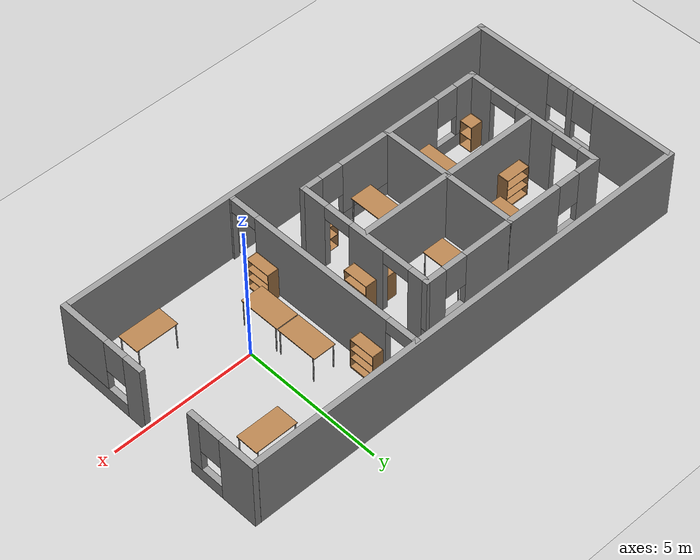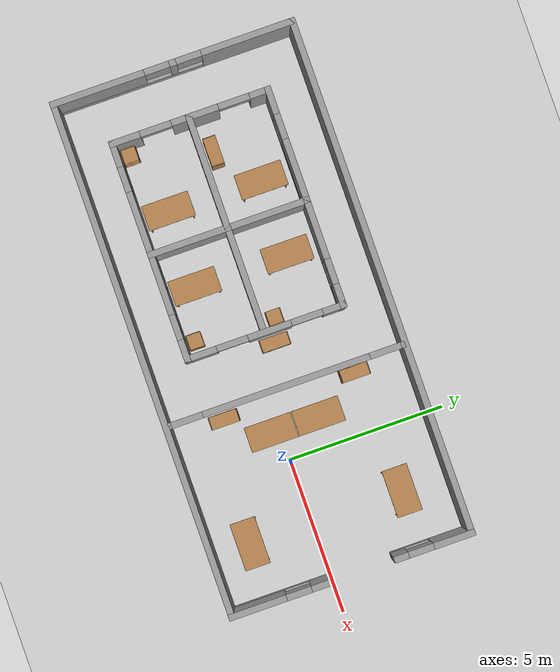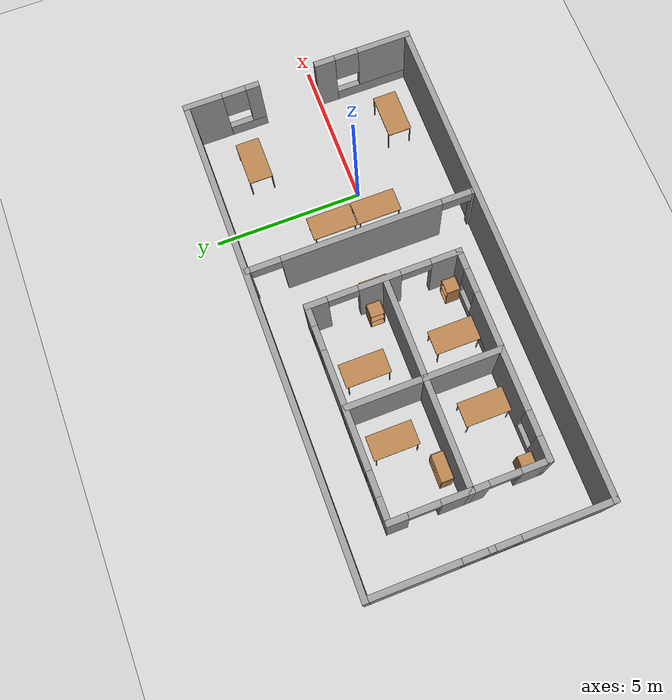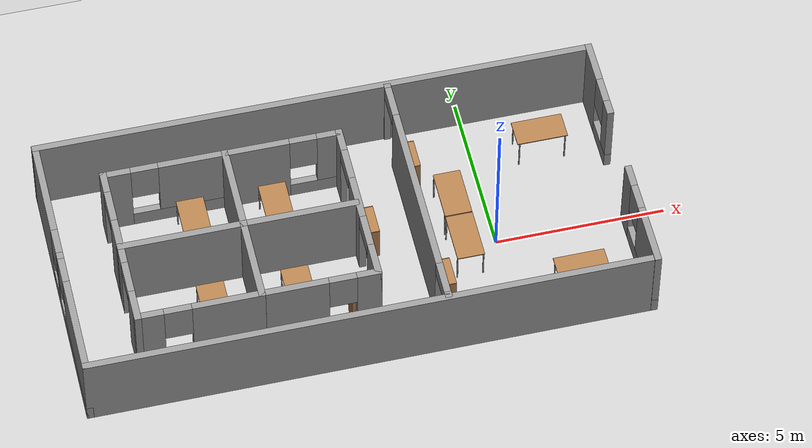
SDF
<sdf version="1.5">
 <world name="default">
  <light name="sun" type="directional">
   <pose>0 0 10 0 -0 0</pose>
   <diffuse>0.8 0.8 0.8 1</diffuse>
   <specular>0.2 0.2 0.2 1</specular>
   <attenuation>
    <range>1000</range>
    <constant>0.9</constant>
    <linear>0.01</linear>
    <quadratic>0.001</quadratic>
   </attenuation>
   <direction>-0.5 0.1 -0.9</direction>
  </light>
  <model name="ground_plane">
   <static>1</static>
   <link name="link">
    <collision name="collision">
     <geometry><plane><normal>0 0 1</normal><size>100 100</size></plane></geometry>
     <surface><friction><ode><mu>100</mu><mu2>50</mu2></ode></friction></surface>
    </collision>
    <visual name="visual">
     <cast_shadows>0</cast_shadows>
     <geometry><plane><normal>0 0 1</normal><size>100 100</size></plane></geometry>
     <material>
      <script><uri>file://media/materials/scripts/gazebo.material</uri><name>Gazebo/Grey</name></script>
     </material>
    </visual>
    <velocity_decay><linear>0</linear><angular>0</angular></velocity_decay>
   </link>
  </model>
  <physics type="ode">
   <max_step_size>0.001</max_step_size>
   <real_time_factor>1</real_time_factor>
   <real_time_update_rate>1000</real_time_update_rate>
   <gravity>0 0 -9.8</gravity>
  </physics>
  <scene><ambient>0.4 0.4 0.4 1</ambient><background>0.7 0.7 0.7 1</background><shadows>1</shadows></scene>
  <spherical_coordinates>
   <surface_model>EARTH_WGS84</surface_model>
   <latitude_deg>0</latitude_deg>
   <longitude_deg>0</longitude_deg>
   <elevation>0</elevation>
   <heading_deg>0</heading_deg>
  </spherical_coordinates>
  <model name="customSmallBuildingOne">
   <pose>-8 3 0 0 -0 0</pose>
   <link name="Wall_10">
    <collision name="Wall_10_Collision">
     <geometry><box><size>2.65184 0.2 2.5</size></box></geometry>
     <pose>0 0 1.25 0 -0 0</pose>
    </collision>
    <visual name="Wall_10_Visual">
     <pose>0 0 1.25 0 -0 0</pose>
     <geometry><box><size>2.65184 0.2 2.5</size></box></geometry>
     <material>
      <script><uri>file://media/materials/scripts/gazebo.material</uri><name>Gazebo/Grey</name></script>
     </material>
    </visual>
    <velocity_decay><linear>0</linear><angular>0</angular></velocity_decay>
    <pose>0.733857 -3.69181 0 0 0 -1.5708</pose>
   </link>
   <link name="Wall_11">
    <pose>-1.03564 -4.91773 0 0 -0 3.14159</pose>
    <visual name="Wall_11_Visual_0">
     <pose>-0.819487 0 1.25 0 -0 0</pose>
     <geometry><box><size>2.10008 0.2 2.5</size></box></geometry>
     <material>
      <script><uri>file://media/materials/scripts/gazebo.material</uri><name>Gazebo/Grey</name></script>
     </material>
    </visual>
    <collision name="Wall_11_Collision_0">
     <geometry><box><size>2.10008 0.2 2.5</size></box></geometry>
     <pose>-0.819487 0 1.25 0 -0 0</pose>
    </collision>
    <visual name="Wall_11_Visual_1">
     <pose>1.05004 0 0.25 0 -0 0</pose>
     <geometry><box><size>1.63897 0.2 0.5</size></box></geometry>
     <material>
      <script><uri>file://media/materials/scripts/gazebo.material</uri><name>Gazebo/Grey</name></script>
     </material>
    </visual>
    <collision name="Wall_11_Collision_1">
     <geometry><box><size>1.63897 0.2 0.5</size></box></geometry>
     <pose>1.05004 0 0.25 0 -0 0</pose>
    </collision>
    <visual name="Wall_11_Visual_2">
     <pose>1.45004 0 1.5 0 -0 0</pose>
     <geometry><box><size>0.838974 0.2 2</size></box></geometry>
     <material>
      <script><uri>file://media/materials/scripts/gazebo.material</uri><name>Gazebo/Grey</name></script>
     </material>
    </visual>
    <collision name="Wall_11_Collision_2">
     <geometry><box><size>0.838974 0.2 2</size></box></geometry>
     <pose>1.45004 0 1.5 0 -0 0</pose>
    </collision>
    <visual name="Wall_11_Visual_3">
     <pose>0.630556 0 1.9 0 -0 0</pose>
     <geometry><box><size>0.8 0.2 1.2</size></box></geometry>
     <material>
      <script><uri>file://media/materials/scripts/gazebo.material</uri><name>Gazebo/Grey</name></script>
     </material>
    </visual>
    <collision name="Wall_11_Collision_3">
     <geometry><box><size>0.8 0.2 1.2</size></box></geometry>
     <pose>0.630556 0 1.9 0 -0 0</pose>
    </collision>
    <velocity_decay><linear>0</linear><angular>0</angular></velocity_decay>
   </link>
   <link name="Wall_12">
    <pose>-2.80513 -3.73807 0 0 -0 1.5708</pose>
    <visual name="Wall_12_Visual_0">
     <pose>-0.787375 0 1.25 0 -0 0</pose>
     <geometry><box><size>0.984572 0.2 2.5</size></box></geometry>
     <material>
      <script><uri>file://media/materials/scripts/gazebo.material</uri><name>Gazebo/Grey</name></script>
     </material>
    </visual>
    <collision name="Wall_12_Collision_0">
     <geometry><box><size>0.984572 0.2 2.5</size></box></geometry>
     <pose>-0.787375 0 1.25 0 -0 0</pose>
    </collision>
    <visual name="Wall_12_Visual_1">
     <pose>0.992286 0 1.25 0 -0 0</pose>
     <geometry><box><size>0.57475 0.2 2.5</size></box></geometry>
     <material>
      <script><uri>file://media/materials/scripts/gazebo.material</uri><name>Gazebo/Grey</name></script>
     </material>
    </visual>
    <collision name="Wall_12_Collision_1">
     <geometry><box><size>0.57475 0.2 2.5</size></box></geometry>
     <pose>0.992286 0 1.25 0 -0 0</pose>
    </collision>
    <visual name="Wall_12_Visual_2">
     <pose>0.204911 0 2.25 0 -0 0</pose>
     <geometry><box><size>1 0.2 0.5</size></box></geometry>
     <material>
      <script><uri>file://media/materials/scripts/gazebo.material</uri><name>Gazebo/Grey</name></script>
     </material>
    </visual>
    <collision name="Wall_12_Collision_2">
     <geometry><box><size>1 0.2 0.5</size></box></geometry>
     <pose>0.204911 0 2.25 0 -0 0</pose>
    </collision>
    <velocity_decay><linear>0</linear><angular>0</angular></velocity_decay>
   </link>
   <link name="Wall_14">
    <pose>2.49225 0.05375 0 0 0 -0.000166</pose>
    <visual name="Wall_14_Visual_0">
     <pose>-0.782153 0 1.25 0 -0 0</pose>
     <geometry><box><size>1.78542 0.2 2.5</size></box></geometry>
     <material>
      <script><uri>file://media/materials/scripts/gazebo.material</uri><name>Gazebo/Grey</name></script>
     </material>
    </visual>
    <collision name="Wall_14_Collision_0">
     <geometry><box><size>1.78542 0.2 2.5</size></box></geometry>
     <pose>-0.782153 0 1.25 0 -0 0</pose>
    </collision>
    <visual name="Wall_14_Visual_1">
     <pose>0.892709 0 0.25 0 -0 0</pose>
     <geometry><box><size>1.56431 0.2 0.5</size></box></geometry>
     <material>
      <script><uri>file://media/materials/scripts/gazebo.material</uri><name>Gazebo/Grey</name></script>
     </material>
    </visual>
    <collision name="Wall_14_Collision_1">
     <geometry><box><size>1.56431 0.2 0.5</size></box></geometry>
     <pose>0.892709 0 0.25 0 -0 0</pose>
    </collision>
    <visual name="Wall_14_Visual_2">
     <pose>1.29271 0 1.5 0 -0 0</pose>
     <geometry><box><size>0.764306 0.2 2</size></box></geometry>
     <material>
      <script><uri>file://media/materials/scripts/gazebo.material</uri><name>Gazebo/Grey</name></script>
     </material>
    </visual>
    <collision name="Wall_14_Collision_2">
     <geometry><box><size>0.764306 0.2 2</size></box></geometry>
     <pose>1.29271 0 1.5 0 -0 0</pose>
    </collision>
    <visual name="Wall_14_Visual_3">
     <pose>0.510556 0 1.9 0 -0 0</pose>
     <geometry><box><size>0.8 0.2 1.2</size></box></geometry>
     <material>
      <script><uri>file://media/materials/scripts/gazebo.material</uri><name>Gazebo/Grey</name></script>
     </material>
    </visual>
    <collision name="Wall_14_Collision_3">
     <geometry><box><size>0.8 0.2 1.2</size></box></geometry>
     <pose>0.510556 0 1.9 0 -0 0</pose>
    </collision>
    <velocity_decay><linear>0</linear><angular>0</angular></velocity_decay>
   </link>
   <link name="Wall_15">
    <pose>4.06697 -2.43328 0 0 0 -1.5708</pose>
    <visual name="Wall_15_Visual_0">
     <pose>-2.21084 0 1.25 0 -0 0</pose>
     <geometry><box><size>0.751862 0.2 2.5</size></box></geometry>
     <material>
      <script><uri>file://media/materials/scripts/gazebo.material</uri><name>Gazebo/Grey</name></script>
     </material>
    </visual>
    <collision name="Wall_15_Collision_0">
     <geometry><box><size>0.751862 0.2 2.5</size></box></geometry>
     <pose>-2.21084 0 1.25 0 -0 0</pose>
    </collision>
    <visual name="Wall_15_Visual_1">
     <pose>-0.143604 0 1.25 0 -0 0</pose>
     <geometry><box><size>1.38261 0.2 2.5</size></box></geometry>
     <material>
      <script><uri>file://media/materials/scripts/gazebo.material</uri><name>Gazebo/Grey</name></script>
     </material>
    </visual>
    <collision name="Wall_15_Collision_1">
     <geometry><box><size>1.38261 0.2 2.5</size></box></geometry>
     <pose>-0.143604 0 1.25 0 -0 0</pose>
    </collision>
    <visual name="Wall_15_Visual_2">
     <pose>2.06724 0 1.25 0 -0 0</pose>
     <geometry><box><size>1.03907 0.2 2.5</size></box></geometry>
     <material>
      <script><uri>file://media/materials/scripts/gazebo.material</uri><name>Gazebo/Grey</name></script>
     </material>
    </visual>
    <collision name="Wall_15_Collision_2">
     <geometry><box><size>1.03907 0.2 2.5</size></box></geometry>
     <pose>2.06724 0 1.25 0 -0 0</pose>
    </collision>
    <visual name="Wall_15_Visual_3">
     <pose>-1.33491 0 2.25 0 -0 0</pose>
     <geometry><box><size>1 0.2 0.5</size></box></geometry>
     <material>
      <script><uri>file://media/materials/scripts/gazebo.material</uri><name>Gazebo/Grey</name></script>
     </material>
    </visual>
    <collision name="Wall_15_Collision_3">
     <geometry><box><size>1 0.2 0.5</size></box></geometry>
     <pose>-1.33491 0 2.25 0 -0 0</pose>
    </collision>
    <visual name="Wall_15_Visual_4">
     <pose>1.0477 0 2.25 0 -0 0</pose>
     <geometry><box><size>1 0.2 0.5</size></box></geometry>
     <material>
      <script><uri>file://media/materials/scripts/gazebo.material</uri><name>Gazebo/Grey</name></script>
     </material>
    </visual>
    <collision name="Wall_15_Collision_4">
     <geometry><box><size>1 0.2 0.5</size></box></geometry>
     <pose>1.0477 0 2.25 0 -0 0</pose>
    </collision>
    <velocity_decay><linear>0</linear><angular>0</angular></velocity_decay>
   </link>
   <link name="Wall_16">
    <pose>2.49625 -4.92005 0 0 -0 3.14159</pose>
    <visual name="Wall_16_Visual_0">
     <pose>-1.31164 0 1.25 0 -0 0</pose>
     <geometry><box><size>0.718161 0.2 2.5</size></box></geometry>
     <material>
      <script><uri>file://media/materials/scripts/gazebo.material</uri><name>Gazebo/Grey</name></script>
     </material>
    </visual>
    <collision name="Wall_16_Collision_0">
     <geometry><box><size>0.718161 0.2 2.5</size></box></geometry>
     <pose>-1.31164 0 1.25 0 -0 0</pose>
    </collision>
    <visual name="Wall_16_Visual_1">
     <pose>0.35908 0 0.25 0 -0 0</pose>
     <geometry><box><size>2.62327 0.2 0.5</size></box></geometry>
     <material>
      <script><uri>file://media/materials/scripts/gazebo.material</uri><name>Gazebo/Grey</name></script>
     </material>
    </visual>
    <collision name="Wall_16_Collision_1">
     <geometry><box><size>2.62327 0.2 0.5</size></box></geometry>
     <pose>0.35908 0 0.25 0 -0 0</pose>
    </collision>
    <visual name="Wall_16_Visual_2">
     <pose>0.75908 0 1.5 0 -0 0</pose>
     <geometry><box><size>1.82327 0.2 2</size></box></geometry>
     <material>
      <script><uri>file://media/materials/scripts/gazebo.material</uri><name>Gazebo/Grey</name></script>
     </material>
    </visual>
    <collision name="Wall_16_Collision_2">
     <geometry><box><size>1.82327 0.2 2</size></box></geometry>
     <pose>0.75908 0 1.5 0 -0 0</pose>
    </collision>
    <visual name="Wall_16_Visual_3">
     <pose>-0.552556 0 1.9 0 -0 0</pose>
     <geometry><box><size>0.8 0.2 1.2</size></box></geometry>
     <material>
      <script><uri>file://media/materials/scripts/gazebo.material</uri><name>Gazebo/Grey</name></script>
     </material>
    </visual>
    <collision name="Wall_16_Collision_3">
     <geometry><box><size>0.8 0.2 1.2</size></box></geometry>
     <pose>-0.552556 0 1.9 0 -0 0</pose>
    </collision>
    <velocity_decay><linear>0</linear><angular>0</angular></velocity_decay>
   </link>
   <link name="Wall_18">
    <collision name="Wall_18_Collision">
     <geometry><box><size>3.35035 0.2 2.5</size></box></geometry>
     <pose>0 0 1.25 0 -0 0</pose>
    </collision>
    <visual name="Wall_18_Visual">
     <pose>0 0 1.25 0 -0 0</pose>
     <geometry><box><size>3.35035 0.2 2.5</size></box></geometry>
     <material>
      <script><uri>file://media/materials/scripts/gazebo.material</uri><name>Gazebo/Grey</name></script>
     </material>
    </visual>
    <velocity_decay><linear>0</linear><angular>0</angular></velocity_decay>
    <pose>2.40459 -2.46784 0 0 -0 0</pose>
   </link>
   <link name="Wall_20">
    <collision name="Wall_20_Collision">
     <geometry><box><size>16.3321 0.2 2.5</size></box></geometry>
     <pose>0 0 1.25 0 -0 0</pose>
    </collision>
    <visual name="Wall_20_Visual">
     <pose>0 0 1.25 0 -0 0</pose>
     <geometry><box><size>16.3321 0.2 2.5</size></box></geometry>
     <material>
      <script><uri>file://media/materials/scripts/gazebo.material</uri><name>Gazebo/Grey</name></script>
     </material>
    </visual>
    <velocity_decay><linear>0</linear><angular>0</angular></velocity_decay>
    <pose>3.54751 1.432 0 0 -0 3.14159</pose>
   </link>
   <link name="Wall_21">
    <pose>-4.51852 -2.38615 0 0 0 -1.5708</pose>
    <visual name="Wall_21_Visual_0">
     <pose>-2.40862 0 1.25 0 -0 0</pose>
     <geometry><box><size>3.01908 0.2 2.5</size></box></geometry>
     <material>
      <script><uri>file://media/materials/scripts/gazebo.material</uri><name>Gazebo/Grey</name></script>
     </material>
    </visual>
    <collision name="Wall_21_Collision_0">
     <geometry><box><size>3.01908 0.2 2.5</size></box></geometry>
     <pose>-2.40862 0 1.25 0 -0 0</pose>
    </collision>
    <visual name="Wall_21_Visual_1">
     <pose>1.50954 0 0.25 0 -0 0</pose>
     <geometry><box><size>4.81724 0.2 0.5</size></box></geometry>
     <material>
      <script><uri>file://media/materials/scripts/gazebo.material</uri><name>Gazebo/Grey</name></script>
     </material>
    </visual>
    <collision name="Wall_21_Collision_1">
     <geometry><box><size>4.81724 0.2 0.5</size></box></geometry>
     <pose>1.50954 0 0.25 0 -0 0</pose>
    </collision>
    <visual name="Wall_21_Visual_2">
     <pose>0.008131 0 1.5 0 -0 0</pose>
     <geometry><box><size>0.214424 0.2 2</size></box></geometry>
     <material>
      <script><uri>file://media/materials/scripts/gazebo.material</uri><name>Gazebo/Grey</name></script>
     </material>
    </visual>
    <collision name="Wall_21_Collision_2">
     <geometry><box><size>0.214424 0.2 2</size></box></geometry>
     <pose>0.008131 0 1.5 0 -0 0</pose>
    </collision>
    <visual name="Wall_21_Visual_3">
     <pose>2.41675 0 1.5 0 -0 0</pose>
     <geometry><box><size>3.00281 0.2 2</size></box></geometry>
     <material>
      <script><uri>file://media/materials/scripts/gazebo.material</uri><name>Gazebo/Grey</name></script>
     </material>
    </visual>
    <collision name="Wall_21_Collision_3">
     <geometry><box><size>3.00281 0.2 2</size></box></geometry>
     <pose>2.41675 0 1.5 0 -0 0</pose>
    </collision>
    <visual name="Wall_21_Visual_4">
     <pose>-0.499081 0 1.9 0 -0 0</pose>
     <geometry><box><size>0.8 0.2 1.2</size></box></geometry>
     <material>
      <script><uri>file://media/materials/scripts/gazebo.material</uri><name>Gazebo/Grey</name></script>
     </material>
    </visual>
    <collision name="Wall_21_Collision_4">
     <geometry><box><size>0.8 0.2 1.2</size></box></geometry>
     <pose>-0.499081 0 1.9 0 -0 0</pose>
    </collision>
    <visual name="Wall_21_Visual_5">
     <pose>0.515343 0 1.9 0 -0 0</pose>
     <geometry><box><size>0.8 0.2 1.2</size></box></geometry>
     <material>
      <script><uri>file://media/materials/scripts/gazebo.material</uri><name>Gazebo/Grey</name></script>
     </material>
    </visual>
    <collision name="Wall_21_Collision_5">
     <geometry><box><size>0.8 0.2 1.2</size></box></geometry>
     <pose>0.515343 0 1.9 0 -0 0</pose>
    </collision>
    <velocity_decay><linear>0</linear><angular>0</angular></velocity_decay>
   </link>
   <link name="Wall_22">
    <collision name="Wall_22_Collision">
     <geometry><box><size>16.332 0.2 2.5</size></box></geometry>
     <pose>0 0 1.25 0 -0 0</pose>
    </collision>
    <visual name="Wall_22_Visual">
     <pose>0 0 1.25 0 -0 0</pose>
     <geometry><box><size>16.332 0.2 2.5</size></box></geometry>
     <material>
      <script><uri>file://media/materials/scripts/gazebo.material</uri><name>Gazebo/Grey</name></script>
     </material>
    </visual>
    <velocity_decay><linear>0</linear><angular>0</angular></velocity_decay>
    <pose>3.54748 -6.20431 0 0 -0 0</pose>
   </link>
   <link name="Wall_26">
    <pose>11.8165 0.244091 0 0 0 -1.5708</pose>
    <visual name="Wall_26_Visual_0">
     <pose>-0.634637 0 1.25 0 -0 0</pose>
     <geometry><box><size>1.30861 0.2 2.5</size></box></geometry>
     <material>
      <script><uri>file://media/materials/scripts/gazebo.material</uri><name>Gazebo/Grey</name></script>
     </material>
    </visual>
    <collision name="Wall_26_Collision_0">
     <geometry><box><size>1.30861 0.2 2.5</size></box></geometry>
     <pose>-0.634637 0 1.25 0 -0 0</pose>
    </collision>
    <visual name="Wall_26_Visual_1">
     <pose>0.654305 0 0.25 0 -0 0</pose>
     <geometry><box><size>1.26927 0.2 0.5</size></box></geometry>
     <material>
      <script><uri>file://media/materials/scripts/gazebo.material</uri><name>Gazebo/Grey</name></script>
     </material>
    </visual>
    <collision name="Wall_26_Collision_1">
     <geometry><box><size>1.26927 0.2 0.5</size></box></geometry>
     <pose>0.654305 0 0.25 0 -0 0</pose>
    </collision>
    <visual name="Wall_26_Visual_2">
     <pose>1.05431 0 1.5 0 -0 0</pose>
     <geometry><box><size>0.469275 0.2 2</size></box></geometry>
     <material>
      <script><uri>file://media/materials/scripts/gazebo.material</uri><name>Gazebo/Grey</name></script>
     </material>
    </visual>
    <collision name="Wall_26_Collision_2">
     <geometry><box><size>0.469275 0.2 2</size></box></geometry>
     <pose>1.05431 0 1.5 0 -0 0</pose>
    </collision>
    <visual name="Wall_26_Visual_3">
     <pose>0.419668 0 1.9 0 -0 0</pose>
     <geometry><box><size>0.8 0.2 1.2</size></box></geometry>
     <material>
      <script><uri>file://media/materials/scripts/gazebo.material</uri><name>Gazebo/Grey</name></script>
     </material>
    </visual>
    <collision name="Wall_26_Collision_3">
     <geometry><box><size>0.8 0.2 1.2</size></box></geometry>
     <pose>0.419668 0 1.9 0 -0 0</pose>
    </collision>
    <velocity_decay><linear>0</linear><angular>0</angular></velocity_decay>
   </link>
   <link name="Wall_28">
    <pose>11.8165 -4.63463 0 0 0 -1.5708</pose>
    <visual name="Wall_28_Visual_0">
     <pose>-1.32234 0 1.25 0 -0 0</pose>
     <geometry><box><size>0.702876 0.2 2.5</size></box></geometry>
     <material>
      <script><uri>file://media/materials/scripts/gazebo.material</uri><name>Gazebo/Grey</name></script>
     </material>
    </visual>
    <collision name="Wall_28_Collision_0">
     <geometry><box><size>0.702876 0.2 2.5</size></box></geometry>
     <pose>-1.32234 0 1.25 0 -0 0</pose>
    </collision>
    <visual name="Wall_28_Visual_1">
     <pose>0.351438 0 0.25 0 -0 0</pose>
     <geometry><box><size>2.64467 0.2 0.5</size></box></geometry>
     <material>
      <script><uri>file://media/materials/scripts/gazebo.material</uri><name>Gazebo/Grey</name></script>
     </material>
    </visual>
    <collision name="Wall_28_Collision_1">
     <geometry><box><size>2.64467 0.2 0.5</size></box></geometry>
     <pose>0.351438 0 0.25 0 -0 0</pose>
    </collision>
    <visual name="Wall_28_Visual_2">
     <pose>0.751438 0 1.5 0 -0 0</pose>
     <geometry><box><size>1.84467 0.2 2</size></box></geometry>
     <material>
      <script><uri>file://media/materials/scripts/gazebo.material</uri><name>Gazebo/Grey</name></script>
     </material>
    </visual>
    <collision name="Wall_28_Collision_2">
     <geometry><box><size>1.84467 0.2 2</size></box></geometry>
     <pose>0.751438 0 1.5 0 -0 0</pose>
    </collision>
    <visual name="Wall_28_Visual_3">
     <pose>-0.570899 0 1.9 0 -0 0</pose>
     <geometry><box><size>0.8 0.2 1.2</size></box></geometry>
     <material>
      <script><uri>file://media/materials/scripts/gazebo.material</uri><name>Gazebo/Grey</name></script>
     </material>
    </visual>
    <collision name="Wall_28_Collision_3">
     <geometry><box><size>0.8 0.2 1.2</size></box></geometry>
     <pose>-0.570899 0 1.9 0 -0 0</pose>
    </collision>
    <velocity_decay><linear>0</linear><angular>0</angular></velocity_decay>
   </link>
   <link name="Wall_30">
    <pose>5.79523 -2.38415 0 0 0 -1.5708</pose>
    <visual name="Wall_30_Visual_0">
     <pose>-3.75962 0 1.25 0 -0 0</pose>
     <geometry><box><size>0.16612 0.2 2.5</size></box></geometry>
     <material>
      <script><uri>file://media/materials/scripts/gazebo.material</uri><name>Gazebo/Grey</name></script>
     </material>
    </visual>
    <collision name="Wall_30_Collision_0">
     <geometry><box><size>0.16612 0.2 2.5</size></box></geometry>
     <pose>-3.75962 0 1.25 0 -0 0</pose>
    </collision>
    <visual name="Wall_30_Visual_1">
     <pose>-0.0137 0 1.25 0 -0 0</pose>
     <geometry><box><size>5.32571 0.2 2.5</size></box></geometry>
     <material>
      <script><uri>file://media/materials/scripts/gazebo.material</uri><name>Gazebo/Grey</name></script>
     </material>
    </visual>
    <collision name="Wall_30_Collision_1">
     <geometry><box><size>5.32571 0.2 2.5</size></box></geometry>
     <pose>-0.0137 0 1.25 0 -0 0</pose>
    </collision>
    <visual name="Wall_30_Visual_2">
     <pose>3.74592 0 1.25 0 -0 0</pose>
     <geometry><box><size>0.193521 0.2 2.5</size></box></geometry>
     <material>
      <script><uri>file://media/materials/scripts/gazebo.material</uri><name>Gazebo/Grey</name></script>
     </material>
    </visual>
    <collision name="Wall_30_Collision_2">
     <geometry><box><size>0.193521 0.2 2.5</size></box></geometry>
     <pose>3.74592 0 1.25 0 -0 0</pose>
    </collision>
    <visual name="Wall_30_Visual_3">
     <pose>-3.17656 0 2.25 0 -0 0</pose>
     <geometry><box><size>1 0.2 0.5</size></box></geometry>
     <material>
      <script><uri>file://media/materials/scripts/gazebo.material</uri><name>Gazebo/Grey</name></script>
     </material>
    </visual>
    <collision name="Wall_30_Collision_3">
     <geometry><box><size>1 0.2 0.5</size></box></geometry>
     <pose>-3.17656 0 2.25 0 -0 0</pose>
    </collision>
    <visual name="Wall_30_Visual_4">
     <pose>3.14915 0 2.25 0 -0 0</pose>
     <geometry><box><size>1 0.2 0.5</size></box></geometry>
     <material>
      <script><uri>file://media/materials/scripts/gazebo.material</uri><name>Gazebo/Grey</name></script>
     </material>
    </visual>
    <collision name="Wall_30_Collision_4">
     <geometry><box><size>1 0.2 0.5</size></box></geometry>
     <pose>3.14915 0 2.25 0 -0 0</pose>
    </collision>
    <velocity_decay><linear>0</linear><angular>0</angular></velocity_decay>
   </link>
   <link name="Wall_5">
    <pose>-1.03527 0.061251 0 0 -0 0</pose>
    <visual name="Wall_5_Visual_0">
     <pose>-1.43006 0 1.25 0 -0 0</pose>
     <geometry><box><size>0.879876 0.2 2.5</size></box></geometry>
     <material>
      <script><uri>file://media/materials/scripts/gazebo.material</uri><name>Gazebo/Grey</name></script>
     </material>
    </visual>
    <collision name="Wall_5_Collision_0">
     <geometry><box><size>0.879876 0.2 2.5</size></box></geometry>
     <pose>-1.43006 0 1.25 0 -0 0</pose>
    </collision>
    <visual name="Wall_5_Visual_1">
     <pose>0.439938 0 0.25 0 -0 0</pose>
     <geometry><box><size>2.86012 0.2 0.5</size></box></geometry>
     <material>
      <script><uri>file://media/materials/scripts/gazebo.material</uri><name>Gazebo/Grey</name></script>
     </material>
    </visual>
    <collision name="Wall_5_Collision_1">
     <geometry><box><size>2.86012 0.2 0.5</size></box></geometry>
     <pose>0.439938 0 0.25 0 -0 0</pose>
    </collision>
    <visual name="Wall_5_Visual_2">
     <pose>0.839938 0 1.5 0 -0 0</pose>
     <geometry><box><size>2.06012 0.2 2</size></box></geometry>
     <material>
      <script><uri>file://media/materials/scripts/gazebo.material</uri><name>Gazebo/Grey</name></script>
     </material>
    </visual>
    <collision name="Wall_5_Collision_2">
     <geometry><box><size>2.06012 0.2 2</size></box></geometry>
     <pose>0.839938 0 1.5 0 -0 0</pose>
    </collision>
    <visual name="Wall_5_Visual_3">
     <pose>-0.590124 0 1.9 0 -0 0</pose>
     <geometry><box><size>0.8 0.2 1.2</size></box></geometry>
     <material>
      <script><uri>file://media/materials/scripts/gazebo.material</uri><name>Gazebo/Grey</name></script>
     </material>
    </visual>
    <collision name="Wall_5_Collision_3">
     <geometry><box><size>0.8 0.2 1.2</size></box></geometry>
     <pose>-0.590124 0 1.9 0 -0 0</pose>
    </collision>
    <velocity_decay><linear>0</linear><angular>0</angular></velocity_decay>
   </link>
   <link name="Wall_6">
    <collision name="Wall_6_Collision">
     <geometry><box><size>2.73 0.2 2.5</size></box></geometry>
     <pose>0 0 1.25 0 -0 0</pose>
    </collision>
    <visual name="Wall_6_Visual">
     <pose>0 0 1.25 0 -0 0</pose>
     <geometry><box><size>2.73 0.2 2.5</size></box></geometry>
     <material>
      <script><uri>file://media/materials/scripts/gazebo.material</uri><name>Gazebo/Grey</name></script>
     </material>
    </visual>
    <velocity_decay><linear>0</linear><angular>0</angular></velocity_decay>
    <pose>0.734733 -1.20375 0 0 0 -1.5708</pose>
   </link>
   <link name="Wall_7">
    <collision name="Wall_7_Collision">
     <geometry><box><size>3.74002 0.2 2.5</size></box></geometry>
     <pose>0 0 1.25 0 -0 0</pose>
    </collision>
    <visual name="Wall_7_Visual">
     <pose>0 0 1.25 0 -0 0</pose>
     <geometry><box><size>3.74002 0.2 2.5</size></box></geometry>
     <material>
      <script><uri>file://media/materials/scripts/gazebo.material</uri><name>Gazebo/Grey</name></script>
     </material>
    </visual>
    <velocity_decay><linear>0</linear><angular>0</angular></velocity_decay>
    <pose>-1.03527 -2.46884 0 0 0 -3.14154</pose>
   </link>
   <link name="Wall_8">
    <pose>-2.80527 -1.20384 0 0 -0 1.5708</pose>
    <visual name="Wall_8_Visual_0">
     <pose>-0.847475 0 1.25 0 -0 0</pose>
     <geometry><box><size>1.03513 0.2 2.5</size></box></geometry>
     <material>
      <script><uri>file://media/materials/scripts/gazebo.material</uri><name>Gazebo/Grey</name></script>
     </material>
    </visual>
    <collision name="Wall_8_Collision_0">
     <geometry><box><size>1.03513 0.2 2.5</size></box></geometry>
     <pose>-0.847475 0 1.25 0 -0 0</pose>
    </collision>
    <visual name="Wall_8_Visual_1">
     <pose>1.01756 0 1.25 0 -0 0</pose>
     <geometry><box><size>0.694951 0.2 2.5</size></box></geometry>
     <material>
      <script><uri>file://media/materials/scripts/gazebo.material</uri><name>Gazebo/Grey</name></script>
     </material>
    </visual>
    <collision name="Wall_8_Collision_1">
     <geometry><box><size>0.694951 0.2 2.5</size></box></geometry>
     <pose>1.01756 0 1.25 0 -0 0</pose>
    </collision>
    <visual name="Wall_8_Visual_2">
     <pose>0.170089 0 2.25 0 -0 0</pose>
     <geometry><box><size>1 0.2 0.5</size></box></geometry>
     <material>
      <script><uri>file://media/materials/scripts/gazebo.material</uri><name>Gazebo/Grey</name></script>
     </material>
    </visual>
    <collision name="Wall_8_Collision_2">
     <geometry><box><size>1 0.2 0.5</size></box></geometry>
     <pose>0.170089 0 2.25 0 -0 0</pose>
    </collision>
    <velocity_decay><linear>0</linear><angular>0</angular></velocity_decay>
   </link>
   <static>1</static>
  </model>
  <model name="table">
   <static>1</static>
   <link name="link">
    <collision name="surface">
     <pose>0 0 1 0 -0 0</pose>
     <geometry><box><size>1.5 0.8 0.03</size></box></geometry>
     <surface><friction><ode><mu>0.6</mu><mu2>0.6</mu2></ode></friction></surface>
    </collision>
    <visual name="visual1">
     <pose>0 0 1 0 -0 0</pose>
     <geometry><box><size>1.5 0.8 0.03</size></box></geometry>
     <material>
      <script><uri>file://media/materials/scripts/gazebo.material</uri><name>Gazebo/Wood</name></script>
     </material>
    </visual>
    <collision name="front_left_leg">
     <pose>0.68 0.38 0.5 0 -0 0</pose>
     <geometry><cylinder><radius>0.02</radius><length>1</length></cylinder></geometry>
    </collision>
    <visual name="front_left_leg">
     <pose>0.68 0.38 0.5 0 -0 0</pose>
     <geometry><cylinder><radius>0.02</radius><length>1</length></cylinder></geometry>
     <material>
      <script><uri>file://media/materials/scripts/gazebo.material</uri><name>Gazebo/Grey</name></script>
     </material>
    </visual>
    <collision name="front_right_leg">
     <pose>0.68 -0.38 0.5 0 -0 0</pose>
     <geometry><cylinder><radius>0.02</radius><length>1</length></cylinder></geometry>
    </collision>
    <visual name="front_right_leg">
     <pose>0.68 -0.38 0.5 0 -0 0</pose>
     <geometry><cylinder><radius>0.02</radius><length>1</length></cylinder></geometry>
     <material>
      <script><uri>file://media/materials/scripts/gazebo.material</uri><name>Gazebo/Grey</name></script>
     </material>
    </visual>
    <collision name="back_right_leg">
     <pose>-0.68 -0.38 0.5 0 -0 0</pose>
     <geometry><cylinder><radius>0.02</radius><length>1</length></cylinder></geometry>
    </collision>
    <visual name="back_right_leg">
     <pose>-0.68 -0.38 0.5 0 -0 0</pose>
     <geometry><cylinder><radius>0.02</radius><length>1</length></cylinder></geometry>
     <material>
      <script><uri>file://media/materials/scripts/gazebo.material</uri><name>Gazebo/Grey</name></script>
     </material>
    </visual>
    <collision name="back_left_leg">
     <pose>-0.68 0.38 0.5 0 -0 0</pose>
     <geometry><cylinder><radius>0.02</radius><length>1</length></cylinder></geometry>
    </collision>
    <visual name="back_left_leg">
     <pose>-0.68 0.38 0.5 0 -0 0</pose>
     <geometry><cylinder><radius>0.02</radius><length>1</length></cylinder></geometry>
     <material>
      <script><uri>file://media/materials/scripts/gazebo.material</uri><name>Gazebo/Grey</name></script>
     </material>
    </visual>
    <velocity_decay><linear>0</linear><angular>0</angular></velocity_decay>
   </link>
   <pose>-6 -1 0 0 -0 1.57</pose>
  </model>
  <model name="table_0">
   <static>1</static>
   <link name="link">
    <collision name="surface">
     <pose>0 0 1 0 -0 0</pose>
     <geometry><box><size>1.5 0.8 0.03</size></box></geometry>
     <surface><friction><ode><mu>0.6</mu><mu2>0.6</mu2></ode></friction></surface>
    </collision>
    <visual name="visual1">
     <pose>0 0 1 0 -0 0</pose>
     <geometry><box><size>1.5 0.8 0.03</size></box></geometry>
     <material>
      <script><uri>file://media/materials/scripts/gazebo.material</uri><name>Gazebo/Wood</name></script>
     </material>
    </visual>
    <collision name="front_left_leg">
     <pose>0.68 0.38 0.5 0 -0 0</pose>
     <geometry><cylinder><radius>0.02</radius><length>1</length></cylinder></geometry>
    </collision>
    <visual name="front_left_leg">
     <pose>0.68 0.38 0.5 0 -0 0</pose>
     <geometry><cylinder><radius>0.02</radius><length>1</length></cylinder></geometry>
     <material>
      <script><uri>file://media/materials/scripts/gazebo.material</uri><name>Gazebo/Grey</name></script>
     </material>
    </visual>
    <collision name="front_right_leg">
     <pose>0.68 -0.38 0.5 0 -0 0</pose>
     <geometry><cylinder><radius>0.02</radius><length>1</length></cylinder></geometry>
    </collision>
    <visual name="front_right_leg">
     <pose>0.68 -0.38 0.5 0 -0 0</pose>
     <geometry><cylinder><radius>0.02</radius><length>1</length></cylinder></geometry>
     <material>
      <script><uri>file://media/materials/scripts/gazebo.material</uri><name>Gazebo/Grey</name></script>
     </material>
    </visual>
    <collision name="back_right_leg">
     <pose>-0.68 -0.38 0.5 0 -0 0</pose>
     <geometry><cylinder><radius>0.02</radius><length>1</length></cylinder></geometry>
    </collision>
    <visual name="back_right_leg">
     <pose>-0.68 -0.38 0.5 0 -0 0</pose>
     <geometry><cylinder><radius>0.02</radius><length>1</length></cylinder></geometry>
     <material>
      <script><uri>file://media/materials/scripts/gazebo.material</uri><name>Gazebo/Grey</name></script>
     </material>
    </visual>
    <collision name="back_left_leg">
     <pose>-0.68 0.38 0.5 0 -0 0</pose>
     <geometry><cylinder><radius>0.02</radius><length>1</length></cylinder></geometry>
    </collision>
    <visual name="back_left_leg">
     <pose>-0.68 0.38 0.5 0 -0 0</pose>
     <geometry><cylinder><radius>0.02</radius><length>1</length></cylinder></geometry>
     <material>
      <script><uri>file://media/materials/scripts/gazebo.material</uri><name>Gazebo/Grey</name></script>
     </material>
    </visual>
    <velocity_decay><linear>0</linear><angular>0</angular></velocity_decay>
   </link>
   <pose>-6 2 0 0 -0 1.57</pose>
  </model>
  <model name="table_1">
   <static>1</static>
   <link name="link">
    <collision name="surface">
     <pose>0 0 1 0 -0 0</pose>
     <geometry><box><size>1.5 0.8 0.03</size></box></geometry>
     <surface><friction><ode><mu>0.6</mu><mu2>0.6</mu2></ode></friction></surface>
    </collision>
    <visual name="visual1">
     <pose>0 0 1 0 -0 0</pose>
     <geometry><box><size>1.5 0.8 0.03</size></box></geometry>
     <material>
      <script><uri>file://media/materials/scripts/gazebo.material</uri><name>Gazebo/Wood</name></script>
     </material>
    </visual>
    <collision name="front_left_leg">
     <pose>0.68 0.38 0.5 0 -0 0</pose>
     <geometry><cylinder><radius>0.02</radius><length>1</length></cylinder></geometry>
    </collision>
    <visual name="front_left_leg">
     <pose>0.68 0.38 0.5 0 -0 0</pose>
     <geometry><cylinder><radius>0.02</radius><length>1</length></cylinder></geometry>
     <material>
      <script><uri>file://media/materials/scripts/gazebo.material</uri><name>Gazebo/Grey</name></script>
     </material>
    </visual>
    <collision name="front_right_leg">
     <pose>0.68 -0.38 0.5 0 -0 0</pose>
     <geometry><cylinder><radius>0.02</radius><length>1</length></cylinder></geometry>
    </collision>
    <visual name="front_right_leg">
     <pose>0.68 -0.38 0.5 0 -0 0</pose>
     <geometry><cylinder><radius>0.02</radius><length>1</length></cylinder></geometry>
     <material>
      <script><uri>file://media/materials/scripts/gazebo.material</uri><name>Gazebo/Grey</name></script>
     </material>
    </visual>
    <collision name="back_right_leg">
     <pose>-0.68 -0.38 0.5 0 -0 0</pose>
     <geometry><cylinder><radius>0.02</radius><length>1</length></cylinder></geometry>
    </collision>
    <visual name="back_right_leg">
     <pose>-0.68 -0.38 0.5 0 -0 0</pose>
     <geometry><cylinder><radius>0.02</radius><length>1</length></cylinder></geometry>
     <material>
      <script><uri>file://media/materials/scripts/gazebo.material</uri><name>Gazebo/Grey</name></script>
     </material>
    </visual>
    <collision name="back_left_leg">
     <pose>-0.68 0.38 0.5 0 -0 0</pose>
     <geometry><cylinder><radius>0.02</radius><length>1</length></cylinder></geometry>
    </collision>
    <visual name="back_left_leg">
     <pose>-0.68 0.38 0.5 0 -0 0</pose>
     <geometry><cylinder><radius>0.02</radius><length>1</length></cylinder></geometry>
     <material>
      <script><uri>file://media/materials/scripts/gazebo.material</uri><name>Gazebo/Grey</name></script>
     </material>
    </visual>
    <velocity_decay><linear>0</linear><angular>0</angular></velocity_decay>
   </link>
   <pose>-8.41122 2 0 0 -0 1.57</pose>
  </model>
  <model name="table_2">
   <static>1</static>
   <link name="link">
    <collision name="surface">
     <pose>0 0 1 0 -0 0</pose>
     <geometry><box><size>1.5 0.8 0.03</size></box></geometry>
     <surface><friction><ode><mu>0.6</mu><mu2>0.6</mu2></ode></friction></surface>
    </collision>
    <visual name="visual1">
     <pose>0 0 1 0 -0 0</pose>
     <geometry><box><size>1.5 0.8 0.03</size></box></geometry>
     <material>
      <script><uri>file://media/materials/scripts/gazebo.material</uri><name>Gazebo/Wood</name></script>
     </material>
    </visual>
    <collision name="front_left_leg">
     <pose>0.68 0.38 0.5 0 -0 0</pose>
     <geometry><cylinder><radius>0.02</radius><length>1</length></cylinder></geometry>
    </collision>
    <visual name="front_left_leg">
     <pose>0.68 0.38 0.5 0 -0 0</pose>
     <geometry><cylinder><radius>0.02</radius><length>1</length></cylinder></geometry>
     <material>
      <script><uri>file://media/materials/scripts/gazebo.material</uri><name>Gazebo/Grey</name></script>
     </material>
    </visual>
    <collision name="front_right_leg">
     <pose>0.68 -0.38 0.5 0 -0 0</pose>
     <geometry><cylinder><radius>0.02</radius><length>1</length></cylinder></geometry>
    </collision>
    <visual name="front_right_leg">
     <pose>0.68 -0.38 0.5 0 -0 0</pose>
     <geometry><cylinder><radius>0.02</radius><length>1</length></cylinder></geometry>
     <material>
      <script><uri>file://media/materials/scripts/gazebo.material</uri><name>Gazebo/Grey</name></script>
     </material>
    </visual>
    <collision name="back_right_leg">
     <pose>-0.68 -0.38 0.5 0 -0 0</pose>
     <geometry><cylinder><radius>0.02</radius><length>1</length></cylinder></geometry>
    </collision>
    <visual name="back_right_leg">
     <pose>-0.68 -0.38 0.5 0 -0 0</pose>
     <geometry><cylinder><radius>0.02</radius><length>1</length></cylinder></geometry>
     <material>
      <script><uri>file://media/materials/scripts/gazebo.material</uri><name>Gazebo/Grey</name></script>
     </material>
    </visual>
    <collision name="back_left_leg">
     <pose>-0.68 0.38 0.5 0 -0 0</pose>
     <geometry><cylinder><radius>0.02</radius><length>1</length></cylinder></geometry>
    </collision>
    <visual name="back_left_leg">
     <pose>-0.68 0.38 0.5 0 -0 0</pose>
     <geometry><cylinder><radius>0.02</radius><length>1</length></cylinder></geometry>
     <material>
      <script><uri>file://media/materials/scripts/gazebo.material</uri><name>Gazebo/Grey</name></script>
     </material>
    </visual>
    <velocity_decay><linear>0</linear><angular>0</angular></velocity_decay>
   </link>
   <pose>-8.45086 -1 0 0 -0 1.57</pose>
  </model>
  <model name="bookshelf">
   <static>1</static>
   <link name="link">
    <inertial><mass>1</mass></inertial>
    <collision name="back">
     <pose>0 0.005 0.6 0 -0 0</pose>
     <geometry><box><size>0.9 0.01 1.2</size></box></geometry>
    </collision>
    <visual name="visual1">
     <pose>0 0.005 0.6 0 -0 0</pose>
     <geometry><box><size>0.9 0.01 1.2</size></box></geometry>
     <material>
      <script><uri>file://media/materials/scripts/gazebo.material</uri><name>Gazebo/Wood</name></script>
     </material>
    </visual>
    <collision name="left_side">
     <pose>0.45 -0.195 0.6 0 -0 0</pose>
     <geometry><box><size>0.02 0.4 1.2</size></box></geometry>
    </collision>
    <visual name="visual2">
     <pose>0.45 -0.195 0.6 0 -0 0</pose>
     <geometry><box><size>0.02 0.4 1.2</size></box></geometry>
     <material>
      <script><uri>file://media/materials/scripts/gazebo.material</uri><name>Gazebo/Wood</name></script>
     </material>
    </visual>
    <collision name="right_side">
     <pose>-0.45 -0.195 0.6 0 -0 0</pose>
     <geometry><box><size>0.02 0.4 1.2</size></box></geometry>
    </collision>
    <visual name="visual3">
     <pose>-0.45 -0.195 0.6 0 -0 0</pose>
     <geometry><box><size>0.02 0.4 1.2</size></box></geometry>
     <material>
      <script><uri>file://media/materials/scripts/gazebo.material</uri><name>Gazebo/Wood</name></script>
     </material>
    </visual>
    <collision name="bottom">
     <pose>0 -0.195 0.03 0 -0 0</pose>
     <geometry><box><size>0.88 0.4 0.06</size></box></geometry>
    </collision>
    <visual name="visual4">
     <pose>0 -0.195 0.03 0 -0 0</pose>
     <geometry><box><size>0.88 0.4 0.06</size></box></geometry>
     <material>
      <script><uri>file://media/materials/scripts/gazebo.material</uri><name>Gazebo/Wood</name></script>
     </material>
    </visual>
    <collision name="top">
     <pose>0 -0.195 1.19 0 -0 0</pose>
     <geometry><box><size>0.88 0.4 0.02</size></box></geometry>
    </collision>
    <visual name="visual5">
     <pose>0 -0.195 1.19 0 -0 0</pose>
     <geometry><box><size>0.88 0.4 0.02</size></box></geometry>
     <material>
      <script><uri>file://media/materials/scripts/gazebo.material</uri><name>Gazebo/Wood</name></script>
     </material>
    </visual>
    <collision name="low_shelf">
     <pose>0 -0.195 0.43 0 -0 0</pose>
     <geometry><box><size>0.88 0.4 0.02</size></box></geometry>
    </collision>
    <visual name="visual6">
     <pose>0 -0.195 0.43 0 -0 0</pose>
     <geometry><box><size>0.88 0.4 0.02</size></box></geometry>
     <material>
      <script><uri>file://media/materials/scripts/gazebo.material</uri><name>Gazebo/Wood</name></script>
     </material>
    </visual>
    <collision name="high_shelf">
     <pose>0 -0.195 0.8 0 -0 0</pose>
     <geometry><box><size>0.88 0.4 0.02</size></box></geometry>
    </collision>
    <visual name="visual7">
     <pose>0 -0.195 0.8 0 -0 0</pose>
     <geometry><box><size>0.88 0.4 0.02</size></box></geometry>
     <material>
      <script><uri>file://media/materials/scripts/gazebo.material</uri><name>Gazebo/Wood</name></script>
     </material>
    </visual>
    <velocity_decay><linear>0</linear><angular>0</angular></velocity_decay>
   </link>
   <pose>-9.71824 0.716207 0 0 -0 3.14</pose>
  </model>
  <model name="bookshelf_0">
   <static>1</static>
   <link name="link">
    <inertial><mass>1</mass></inertial>
    <collision name="back">
     <pose>0 0.005 0.6 0 -0 0</pose>
     <geometry><box><size>0.9 0.01 1.2</size></box></geometry>
    </collision>
    <visual name="visual1">
     <pose>0 0.005 0.6 0 -0 0</pose>
     <geometry><box><size>0.9 0.01 1.2</size></box></geometry>
     <material>
      <script><uri>file://media/materials/scripts/gazebo.material</uri><name>Gazebo/Wood</name></script>
     </material>
    </visual>
    <collision name="left_side">
     <pose>0.45 -0.195 0.6 0 -0 0</pose>
     <geometry><box><size>0.02 0.4 1.2</size></box></geometry>
    </collision>
    <visual name="visual2">
     <pose>0.45 -0.195 0.6 0 -0 0</pose>
     <geometry><box><size>0.02 0.4 1.2</size></box></geometry>
     <material>
      <script><uri>file://media/materials/scripts/gazebo.material</uri><name>Gazebo/Wood</name></script>
     </material>
    </visual>
    <collision name="right_side">
     <pose>-0.45 -0.195 0.6 0 -0 0</pose>
     <geometry><box><size>0.02 0.4 1.2</size></box></geometry>
    </collision>
    <visual name="visual3">
     <pose>-0.45 -0.195 0.6 0 -0 0</pose>
     <geometry><box><size>0.02 0.4 1.2</size></box></geometry>
     <material>
      <script><uri>file://media/materials/scripts/gazebo.material</uri><name>Gazebo/Wood</name></script>
     </material>
    </visual>
    <collision name="bottom">
     <pose>0 -0.195 0.03 0 -0 0</pose>
     <geometry><box><size>0.88 0.4 0.06</size></box></geometry>
    </collision>
    <visual name="visual4">
     <pose>0 -0.195 0.03 0 -0 0</pose>
     <geometry><box><size>0.88 0.4 0.06</size></box></geometry>
     <material>
      <script><uri>file://media/materials/scripts/gazebo.material</uri><name>Gazebo/Wood</name></script>
     </material>
    </visual>
    <collision name="top">
     <pose>0 -0.195 1.19 0 -0 0</pose>
     <geometry><box><size>0.88 0.4 0.02</size></box></geometry>
    </collision>
    <visual name="visual5">
     <pose>0 -0.195 1.19 0 -0 0</pose>
     <geometry><box><size>0.88 0.4 0.02</size></box></geometry>
     <material>
      <script><uri>file://media/materials/scripts/gazebo.material</uri><name>Gazebo/Wood</name></script>
     </material>
    </visual>
    <collision name="low_shelf">
     <pose>0 -0.195 0.43 0 -0 0</pose>
     <geometry><box><size>0.88 0.4 0.02</size></box></geometry>
    </collision>
    <visual name="visual6">
     <pose>0 -0.195 0.43 0 -0 0</pose>
     <geometry><box><size>0.88 0.4 0.02</size></box></geometry>
     <material>
      <script><uri>file://media/materials/scripts/gazebo.material</uri><name>Gazebo/Wood</name></script>
     </material>
    </visual>
    <collision name="high_shelf">
     <pose>0 -0.195 0.8 0 -0 0</pose>
     <geometry><box><size>0.88 0.4 0.02</size></box></geometry>
    </collision>
    <visual name="visual7">
     <pose>0 -0.195 0.8 0 -0 0</pose>
     <geometry><box><size>0.88 0.4 0.02</size></box></geometry>
     <material>
      <script><uri>file://media/materials/scripts/gazebo.material</uri><name>Gazebo/Wood</name></script>
     </material>
    </visual>
    <velocity_decay><linear>0</linear><angular>0</angular></velocity_decay>
   </link>
   <pose>-3.76364 0.752676 0 0 -0 1.57</pose>
  </model>
  <model name="cabinet">
   <static>1</static>
   <link name="cabinet_bottom_plate">
    <inertial>
     <pose>0 0 -1 0 -0 0</pose>
     <inertia><ixx>2.05</ixx><ixy>0</ixy><ixz>0</ixz><iyy>2.05</iyy><iyz>0</iyz><izz>2.05</izz></inertia>
     <mass>25</mass>
    </inertial>
    <collision name="cabinet_bottom_plate_geom">
     <pose>0 0 0.01 0 -0 0</pose>
     <geometry><box><size>0.45 0.45 0.02</size></box></geometry>
    </collision>
    <visual name="cabinet_bottom_plate_geom_visual">
     <pose>0 0 0.01 0 -0 0</pose>
     <geometry><box><size>0.45 0.45 0.02</size></box></geometry>
     <material>
      <script><uri>file://media/materials/scripts/gazebo.material</uri><name>Gazebo/Wood</name></script>
     </material>
    </visual>
    <collision name="cabinet_bottom_plate_geom_cabinet_back_plate">
     <pose>0.235 0 0.51 0 -0 0</pose>
     <geometry><box><size>0.02 0.45 1.02</size></box></geometry>
    </collision>
    <visual name="cabinet_bottom_plate_geom_cabinet_back_plate_visual">
     <pose>0.235 0 0.51 0 -0 0</pose>
     <geometry><box><size>0.02 0.45 1.02</size></box></geometry>
     <material>
      <script><uri>file://media/materials/scripts/gazebo.material</uri><name>Gazebo/Wood</name></script>
     </material>
    </visual>
    <collision name="cabinet_bottom_plate_geom_cabinet_left_plate">
     <pose>0 0.235 0.51 0 -0 0</pose>
     <geometry><box><size>0.45 0.02 1.02</size></box></geometry>
    </collision>
    <visual name="cabinet_bottom_plate_geom_cabinet_left_plate_visual">
     <pose>0 0.235 0.51 0 -0 0</pose>
     <geometry><box><size>0.45 0.02 1.02</size></box></geometry>
     <material>
      <script><uri>file://media/materials/scripts/gazebo.material</uri><name>Gazebo/Wood</name></script>
     </material>
    </visual>
    <collision name="cabinet_bottom_plate_geom_cabinet_middle_plate">
     <pose>0 0 0.51 0 -0 0</pose>
     <geometry><box><size>0.45 0.45 0.02</size></box></geometry>
    </collision>
    <visual name="cabinet_bottom_plate_geom_cabinet_middle_plate_visual">
     <pose>0 0 0.51 0 -0 0</pose>
     <geometry><box><size>0.45 0.45 0.02</size></box></geometry>
     <material>
      <script><uri>file://media/materials/scripts/gazebo.material</uri><name>Gazebo/Wood</name></script>
     </material>
    </visual>
    <collision name="cabinet_bottom_plate_geom_cabinet_right_plate">
     <pose>0 -0.235 0.51 0 -0 0</pose>
     <geometry><box><size>0.45 0.02 1.02</size></box></geometry>
    </collision>
    <visual name="cabinet_bottom_plate_geom_cabinet_right_plate_visual">
     <pose>0 -0.235 0.51 0 -0 0</pose>
     <geometry><box><size>0.45 0.02 1.02</size></box></geometry>
     <material>
      <script><uri>file://media/materials/scripts/gazebo.material</uri><name>Gazebo/Wood</name></script>
     </material>
    </visual>
    <collision name="cabinet_bottom_plate_geom_cabinet_top_plate">
     <pose>0 0 1.01 0 -0 0</pose>
     <geometry><box><size>0.45 0.45 0.02</size></box></geometry>
    </collision>
    <visual name="cabinet_bottom_plate_geom_cabinet_top_plate_visual">
     <pose>0 0 1.01 0 -0 0</pose>
     <geometry><box><size>0.45 0.45 0.02</size></box></geometry>
     <material>
      <script><uri>file://media/materials/scripts/gazebo.material</uri><name>Gazebo/Wood</name></script>
     </material>
    </visual>
    <velocity_decay><linear>0</linear><angular>0</angular></velocity_decay>
   </link>
   <pose>-4.41546 -1.53797 0 0 0 -1.57</pose>
  </model>
  <model name="cabinet_0">
   <static>1</static>
   <link name="cabinet_bottom_plate">
    <inertial>
     <pose>0 0 -1 0 -0 0</pose>
     <inertia><ixx>2.05</ixx><ixy>0</ixy><ixz>0</ixz><iyy>2.05</iyy><iyz>0</iyz><izz>2.05</izz></inertia>
     <mass>25</mass>
    </inertial>
    <collision name="cabinet_bottom_plate_geom">
     <pose>0 0 0.01 0 -0 0</pose>
     <geometry><box><size>0.45 0.45 0.02</size></box></geometry>
    </collision>
    <visual name="cabinet_bottom_plate_geom_visual">
     <pose>0 0 0.01 0 -0 0</pose>
     <geometry><box><size>0.45 0.45 0.02</size></box></geometry>
     <material>
      <script><uri>file://media/materials/scripts/gazebo.material</uri><name>Gazebo/Wood</name></script>
     </material>
    </visual>
    <collision name="cabinet_bottom_plate_geom_cabinet_back_plate">
     <pose>0.235 0 0.51 0 -0 0</pose>
     <geometry><box><size>0.02 0.45 1.02</size></box></geometry>
    </collision>
    <visual name="cabinet_bottom_plate_geom_cabinet_back_plate_visual">
     <pose>0.235 0 0.51 0 -0 0</pose>
     <geometry><box><size>0.02 0.45 1.02</size></box></geometry>
     <material>
      <script><uri>file://media/materials/scripts/gazebo.material</uri><name>Gazebo/Wood</name></script>
     </material>
    </visual>
    <collision name="cabinet_bottom_plate_geom_cabinet_left_plate">
     <pose>0 0.235 0.51 0 -0 0</pose>
     <geometry><box><size>0.45 0.02 1.02</size></box></geometry>
    </collision>
    <visual name="cabinet_bottom_plate_geom_cabinet_left_plate_visual">
     <pose>0 0.235 0.51 0 -0 0</pose>
     <geometry><box><size>0.45 0.02 1.02</size></box></geometry>
     <material>
      <script><uri>file://media/materials/scripts/gazebo.material</uri><name>Gazebo/Wood</name></script>
     </material>
    </visual>
    <collision name="cabinet_bottom_plate_geom_cabinet_middle_plate">
     <pose>0 0 0.51 0 -0 0</pose>
     <geometry><box><size>0.45 0.45 0.02</size></box></geometry>
    </collision>
    <visual name="cabinet_bottom_plate_geom_cabinet_middle_plate_visual">
     <pose>0 0 0.51 0 -0 0</pose>
     <geometry><box><size>0.45 0.45 0.02</size></box></geometry>
     <material>
      <script><uri>file://media/materials/scripts/gazebo.material</uri><name>Gazebo/Wood</name></script>
     </material>
    </visual>
    <collision name="cabinet_bottom_plate_geom_cabinet_right_plate">
     <pose>0 -0.235 0.51 0 -0 0</pose>
     <geometry><box><size>0.45 0.02 1.02</size></box></geometry>
    </collision>
    <visual name="cabinet_bottom_plate_geom_cabinet_right_plate_visual">
     <pose>0 -0.235 0.51 0 -0 0</pose>
     <geometry><box><size>0.45 0.02 1.02</size></box></geometry>
     <material>
      <script><uri>file://media/materials/scripts/gazebo.material</uri><name>Gazebo/Wood</name></script>
     </material>
    </visual>
    <collision name="cabinet_bottom_plate_geom_cabinet_top_plate">
     <pose>0 0 1.01 0 -0 0</pose>
     <geometry><box><size>0.45 0.45 0.02</size></box></geometry>
    </collision>
    <visual name="cabinet_bottom_plate_geom_cabinet_top_plate_visual">
     <pose>0 0 1.01 0 -0 0</pose>
     <geometry><box><size>0.45 0.45 0.02</size></box></geometry>
     <material>
      <script><uri>file://media/materials/scripts/gazebo.material</uri><name>Gazebo/Wood</name></script>
     </material>
    </visual>
    <velocity_decay><linear>0</linear><angular>0</angular></velocity_decay>
   </link>
   <pose>-10.454 -1.5596 0 0 -0 3.14</pose>
  </model>
  <model name="cabinet_1">
   <static>1</static>
   <link name="cabinet_bottom_plate">
    <inertial>
     <pose>0 0 -1 0 -0 0</pose>
     <inertia><ixx>2.05</ixx><ixy>0</ixy><ixz>0</ixz><iyy>2.05</iyy><iyz>0</iyz><izz>2.05</izz></inertia>
     <mass>25</mass>
    </inertial>
    <collision name="cabinet_bottom_plate_geom">
     <pose>0 0 0.01 0 -0 0</pose>
     <geometry><box><size>0.45 0.45 0.02</size></box></geometry>
    </collision>
    <visual name="cabinet_bottom_plate_geom_visual">
     <pose>0 0 0.01 0 -0 0</pose>
     <geometry><box><size>0.45 0.45 0.02</size></box></geometry>
     <material>
      <script><uri>file://media/materials/scripts/gazebo.material</uri><name>Gazebo/Wood</name></script>
     </material>
    </visual>
    <collision name="cabinet_bottom_plate_geom_cabinet_back_plate">
     <pose>0.235 0 0.51 0 -0 0</pose>
     <geometry><box><size>0.02 0.45 1.02</size></box></geometry>
    </collision>
    <visual name="cabinet_bottom_plate_geom_cabinet_back_plate_visual">
     <pose>0.235 0 0.51 0 -0 0</pose>
     <geometry><box><size>0.02 0.45 1.02</size></box></geometry>
     <material>
      <script><uri>file://media/materials/scripts/gazebo.material</uri><name>Gazebo/Wood</name></script>
     </material>
    </visual>
    <collision name="cabinet_bottom_plate_geom_cabinet_left_plate">
     <pose>0 0.235 0.51 0 -0 0</pose>
     <geometry><box><size>0.45 0.02 1.02</size></box></geometry>
    </collision>
    <visual name="cabinet_bottom_plate_geom_cabinet_left_plate_visual">
     <pose>0 0.235 0.51 0 -0 0</pose>
     <geometry><box><size>0.45 0.02 1.02</size></box></geometry>
     <material>
      <script><uri>file://media/materials/scripts/gazebo.material</uri><name>Gazebo/Wood</name></script>
     </material>
    </visual>
    <collision name="cabinet_bottom_plate_geom_cabinet_middle_plate">
     <pose>0 0 0.51 0 -0 0</pose>
     <geometry><box><size>0.45 0.45 0.02</size></box></geometry>
    </collision>
    <visual name="cabinet_bottom_plate_geom_cabinet_middle_plate_visual">
     <pose>0 0 0.51 0 -0 0</pose>
     <geometry><box><size>0.45 0.45 0.02</size></box></geometry>
     <material>
      <script><uri>file://media/materials/scripts/gazebo.material</uri><name>Gazebo/Wood</name></script>
     </material>
    </visual>
    <collision name="cabinet_bottom_plate_geom_cabinet_right_plate">
     <pose>0 -0.235 0.51 0 -0 0</pose>
     <geometry><box><size>0.45 0.02 1.02</size></box></geometry>
    </collision>
    <visual name="cabinet_bottom_plate_geom_cabinet_right_plate_visual">
     <pose>0 -0.235 0.51 0 -0 0</pose>
     <geometry><box><size>0.45 0.02 1.02</size></box></geometry>
     <material>
      <script><uri>file://media/materials/scripts/gazebo.material</uri><name>Gazebo/Wood</name></script>
     </material>
    </visual>
    <collision name="cabinet_bottom_plate_geom_cabinet_top_plate">
     <pose>0 0 1.01 0 -0 0</pose>
     <geometry><box><size>0.45 0.45 0.02</size></box></geometry>
    </collision>
    <visual name="cabinet_bottom_plate_geom_cabinet_top_plate_visual">
     <pose>0 0 1.01 0 -0 0</pose>
     <geometry><box><size>0.45 0.45 0.02</size></box></geometry>
     <material>
      <script><uri>file://media/materials/scripts/gazebo.material</uri><name>Gazebo/Wood</name></script>
     </material>
    </visual>
    <velocity_decay><linear>0</linear><angular>0</angular></velocity_decay>
   </link>
   <pose>-4.31158 1.00055 0 0 -0 0</pose>
  </model>
  <model name="table_3">
   <static>1</static>
   <link name="link">
    <collision name="surface">
     <pose>0 0 1 0 -0 0</pose>
     <geometry><box><size>1.5 0.8 0.03</size></box></geometry>
     <surface><friction><ode><mu>0.6</mu><mu2>0.6</mu2></ode></friction></surface>
    </collision>
    <visual name="visual1">
     <pose>0 0 1 0 -0 0</pose>
     <geometry><box><size>1.5 0.8 0.03</size></box></geometry>
     <material>
      <script><uri>file://media/materials/scripts/gazebo.material</uri><name>Gazebo/Wood</name></script>
     </material>
    </visual>
    <collision name="front_left_leg">
     <pose>0.68 0.38 0.5 0 -0 0</pose>
     <geometry><cylinder><radius>0.02</radius><length>1</length></cylinder></geometry>
    </collision>
    <visual name="front_left_leg">
     <pose>0.68 0.38 0.5 0 -0 0</pose>
     <geometry><cylinder><radius>0.02</radius><length>1</length></cylinder></geometry>
     <material>
      <script><uri>file://media/materials/scripts/gazebo.material</uri><name>Gazebo/Grey</name></script>
     </material>
    </visual>
    <collision name="front_right_leg">
     <pose>0.68 -0.38 0.5 0 -0 0</pose>
     <geometry><cylinder><radius>0.02</radius><length>1</length></cylinder></geometry>
    </collision>
    <visual name="front_right_leg">
     <pose>0.68 -0.38 0.5 0 -0 0</pose>
     <geometry><cylinder><radius>0.02</radius><length>1</length></cylinder></geometry>
     <material>
      <script><uri>file://media/materials/scripts/gazebo.material</uri><name>Gazebo/Grey</name></script>
     </material>
    </visual>
    <collision name="back_right_leg">
     <pose>-0.68 -0.38 0.5 0 -0 0</pose>
     <geometry><cylinder><radius>0.02</radius><length>1</length></cylinder></geometry>
    </collision>
    <visual name="back_right_leg">
     <pose>-0.68 -0.38 0.5 0 -0 0</pose>
     <geometry><cylinder><radius>0.02</radius><length>1</length></cylinder></geometry>
     <material>
      <script><uri>file://media/materials/scripts/gazebo.material</uri><name>Gazebo/Grey</name></script>
     </material>
    </visual>
    <collision name="back_left_leg">
     <pose>-0.68 0.38 0.5 0 -0 0</pose>
     <geometry><cylinder><radius>0.02</radius><length>1</length></cylinder></geometry>
    </collision>
    <visual name="back_left_leg">
     <pose>-0.68 0.38 0.5 0 -0 0</pose>
     <geometry><cylinder><radius>0.02</radius><length>1</length></cylinder></geometry>
     <material>
      <script><uri>file://media/materials/scripts/gazebo.material</uri><name>Gazebo/Grey</name></script>
     </material>
    </visual>
    <velocity_decay><linear>0</linear><angular>0</angular></velocity_decay>
   </link>
   <pose>2 -2 0 0 -0 0</pose>
  </model>
  <model name="table_4">
   <static>1</static>
   <link name="link">
    <collision name="surface">
     <pose>0 0 1 0 -0 0</pose>
     <geometry><box><size>1.5 0.8 0.03</size></box></geometry>
     <surface><friction><ode><mu>0.6</mu><mu2>0.6</mu2></ode></friction></surface>
    </collision>
    <visual name="visual1">
     <pose>0 0 1 0 -0 0</pose>
     <geometry><box><size>1.5 0.8 0.03</size></box></geometry>
     <material>
      <script><uri>file://media/materials/scripts/gazebo.material</uri><name>Gazebo/Wood</name></script>
     </material>
    </visual>
    <collision name="front_left_leg">
     <pose>0.68 0.38 0.5 0 -0 0</pose>
     <geometry><cylinder><radius>0.02</radius><length>1</length></cylinder></geometry>
    </collision>
    <visual name="front_left_leg">
     <pose>0.68 0.38 0.5 0 -0 0</pose>
     <geometry><cylinder><radius>0.02</radius><length>1</length></cylinder></geometry>
     <material>
      <script><uri>file://media/materials/scripts/gazebo.material</uri><name>Gazebo/Grey</name></script>
     </material>
    </visual>
    <collision name="front_right_leg">
     <pose>0.68 -0.38 0.5 0 -0 0</pose>
     <geometry><cylinder><radius>0.02</radius><length>1</length></cylinder></geometry>
    </collision>
    <visual name="front_right_leg">
     <pose>0.68 -0.38 0.5 0 -0 0</pose>
     <geometry><cylinder><radius>0.02</radius><length>1</length></cylinder></geometry>
     <material>
      <script><uri>file://media/materials/scripts/gazebo.material</uri><name>Gazebo/Grey</name></script>
     </material>
    </visual>
    <collision name="back_right_leg">
     <pose>-0.68 -0.38 0.5 0 -0 0</pose>
     <geometry><cylinder><radius>0.02</radius><length>1</length></cylinder></geometry>
    </collision>
    <visual name="back_right_leg">
     <pose>-0.68 -0.38 0.5 0 -0 0</pose>
     <geometry><cylinder><radius>0.02</radius><length>1</length></cylinder></geometry>
     <material>
      <script><uri>file://media/materials/scripts/gazebo.material</uri><name>Gazebo/Grey</name></script>
     </material>
    </visual>
    <collision name="back_left_leg">
     <pose>-0.68 0.38 0.5 0 -0 0</pose>
     <geometry><cylinder><radius>0.02</radius><length>1</length></cylinder></geometry>
    </collision>
    <visual name="back_left_leg">
     <pose>-0.68 0.38 0.5 0 -0 0</pose>
     <geometry><cylinder><radius>0.02</radius><length>1</length></cylinder></geometry>
     <material>
      <script><uri>file://media/materials/scripts/gazebo.material</uri><name>Gazebo/Grey</name></script>
     </material>
    </visual>
    <velocity_decay><linear>0</linear><angular>0</angular></velocity_decay>
   </link>
   <pose>2 2.92871 0 0 -0 0</pose>
  </model>
  <model name="table_5">
   <static>1</static>
   <link name="link">
    <collision name="surface">
     <pose>0 0 1 0 -0 0</pose>
     <geometry><box><size>1.5 0.8 0.03</size></box></geometry>
     <surface><friction><ode><mu>0.6</mu><mu2>0.6</mu2></ode></friction></surface>
    </collision>
    <visual name="visual1">
     <pose>0 0 1 0 -0 0</pose>
     <geometry><box><size>1.5 0.8 0.03</size></box></geometry>
     <material>
      <script><uri>file://media/materials/scripts/gazebo.material</uri><name>Gazebo/Wood</name></script>
     </material>
    </visual>
    <collision name="front_left_leg">
     <pose>0.68 0.38 0.5 0 -0 0</pose>
     <geometry><cylinder><radius>0.02</radius><length>1</length></cylinder></geometry>
    </collision>
    <visual name="front_left_leg">
     <pose>0.68 0.38 0.5 0 -0 0</pose>
     <geometry><cylinder><radius>0.02</radius><length>1</length></cylinder></geometry>
     <material>
      <script><uri>file://media/materials/scripts/gazebo.material</uri><name>Gazebo/Grey</name></script>
     </material>
    </visual>
    <collision name="front_right_leg">
     <pose>0.68 -0.38 0.5 0 -0 0</pose>
     <geometry><cylinder><radius>0.02</radius><length>1</length></cylinder></geometry>
    </collision>
    <visual name="front_right_leg">
     <pose>0.68 -0.38 0.5 0 -0 0</pose>
     <geometry><cylinder><radius>0.02</radius><length>1</length></cylinder></geometry>
     <material>
      <script><uri>file://media/materials/scripts/gazebo.material</uri><name>Gazebo/Grey</name></script>
     </material>
    </visual>
    <collision name="back_right_leg">
     <pose>-0.68 -0.38 0.5 0 -0 0</pose>
     <geometry><cylinder><radius>0.02</radius><length>1</length></cylinder></geometry>
    </collision>
    <visual name="back_right_leg">
     <pose>-0.68 -0.38 0.5 0 -0 0</pose>
     <geometry><cylinder><radius>0.02</radius><length>1</length></cylinder></geometry>
     <material>
      <script><uri>file://media/materials/scripts/gazebo.material</uri><name>Gazebo/Grey</name></script>
     </material>
    </visual>
    <collision name="back_left_leg">
     <pose>-0.68 0.38 0.5 0 -0 0</pose>
     <geometry><cylinder><radius>0.02</radius><length>1</length></cylinder></geometry>
    </collision>
    <visual name="back_left_leg">
     <pose>-0.68 0.38 0.5 0 -0 0</pose>
     <geometry><cylinder><radius>0.02</radius><length>1</length></cylinder></geometry>
     <material>
      <script><uri>file://media/materials/scripts/gazebo.material</uri><name>Gazebo/Grey</name></script>
     </material>
    </visual>
    <velocity_decay><linear>0</linear><angular>0</angular></velocity_decay>
   </link>
   <pose>-0.999414 -0.264536 0 0 -0 1.57</pose>
  </model>
  <model name="table_6">
   <static>1</static>
   <link name="link">
    <collision name="surface">
     <pose>0 0 1 0 -0 0</pose>
     <geometry><box><size>1.5 0.8 0.03</size></box></geometry>
     <surface><friction><ode><mu>0.6</mu><mu2>0.6</mu2></ode></friction></surface>
    </collision>
    <visual name="visual1">
     <pose>0 0 1 0 -0 0</pose>
     <geometry><box><size>1.5 0.8 0.03</size></box></geometry>
     <material>
      <script><uri>file://media/materials/scripts/gazebo.material</uri><name>Gazebo/Wood</name></script>
     </material>
    </visual>
    <collision name="front_left_leg">
     <pose>0.68 0.38 0.5 0 -0 0</pose>
     <geometry><cylinder><radius>0.02</radius><length>1</length></cylinder></geometry>
    </collision>
    <visual name="front_left_leg">
     <pose>0.68 0.38 0.5 0 -0 0</pose>
     <geometry><cylinder><radius>0.02</radius><length>1</length></cylinder></geometry>
     <material>
      <script><uri>file://media/materials/scripts/gazebo.material</uri><name>Gazebo/Grey</name></script>
     </material>
    </visual>
    <collision name="front_right_leg">
     <pose>0.68 -0.38 0.5 0 -0 0</pose>
     <geometry><cylinder><radius>0.02</radius><length>1</length></cylinder></geometry>
    </collision>
    <visual name="front_right_leg">
     <pose>0.68 -0.38 0.5 0 -0 0</pose>
     <geometry><cylinder><radius>0.02</radius><length>1</length></cylinder></geometry>
     <material>
      <script><uri>file://media/materials/scripts/gazebo.material</uri><name>Gazebo/Grey</name></script>
     </material>
    </visual>
    <collision name="back_right_leg">
     <pose>-0.68 -0.38 0.5 0 -0 0</pose>
     <geometry><cylinder><radius>0.02</radius><length>1</length></cylinder></geometry>
    </collision>
    <visual name="back_right_leg">
     <pose>-0.68 -0.38 0.5 0 -0 0</pose>
     <geometry><cylinder><radius>0.02</radius><length>1</length></cylinder></geometry>
     <material>
      <script><uri>file://media/materials/scripts/gazebo.material</uri><name>Gazebo/Grey</name></script>
     </material>
    </visual>
    <collision name="back_left_leg">
     <pose>-0.68 0.38 0.5 0 -0 0</pose>
     <geometry><cylinder><radius>0.02</radius><length>1</length></cylinder></geometry>
    </collision>
    <visual name="back_left_leg">
     <pose>-0.68 0.38 0.5 0 -0 0</pose>
     <geometry><cylinder><radius>0.02</radius><length>1</length></cylinder></geometry>
     <material>
      <script><uri>file://media/materials/scripts/gazebo.material</uri><name>Gazebo/Grey</name></script>
     </material>
    </visual>
    <velocity_decay><linear>0</linear><angular>0</angular></velocity_decay>
   </link>
   <pose>-0.999787 1.2674 0 0 -0 1.57</pose>
  </model>
  <model name="bookshelf_1">
   <static>1</static>
   <link name="link">
    <inertial><mass>1</mass></inertial>
    <collision name="back">
     <pose>0 0.005 0.6 0 -0 0</pose>
     <geometry><box><size>0.9 0.01 1.2</size></box></geometry>
    </collision>
    <visual name="visual1">
     <pose>0 0.005 0.6 0 -0 0</pose>
     <geometry><box><size>0.9 0.01 1.2</size></box></geometry>
     <material>
      <script><uri>file://media/materials/scripts/gazebo.material</uri><name>Gazebo/Wood</name></script>
     </material>
    </visual>
    <collision name="left_side">
     <pose>0.45 -0.195 0.6 0 -0 0</pose>
     <geometry><box><size>0.02 0.4 1.2</size></box></geometry>
    </collision>
    <visual name="visual2">
     <pose>0.45 -0.195 0.6 0 -0 0</pose>
     <geometry><box><size>0.02 0.4 1.2</size></box></geometry>
     <material>
      <script><uri>file://media/materials/scripts/gazebo.material</uri><name>Gazebo/Wood</name></script>
     </material>
    </visual>
    <collision name="right_side">
     <pose>-0.45 -0.195 0.6 0 -0 0</pose>
     <geometry><box><size>0.02 0.4 1.2</size></box></geometry>
    </collision>
    <visual name="visual3">
     <pose>-0.45 -0.195 0.6 0 -0 0</pose>
     <geometry><box><size>0.02 0.4 1.2</size></box></geometry>
     <material>
      <script><uri>file://media/materials/scripts/gazebo.material</uri><name>Gazebo/Wood</name></script>
     </material>
    </visual>
    <collision name="bottom">
     <pose>0 -0.195 0.03 0 -0 0</pose>
     <geometry><box><size>0.88 0.4 0.06</size></box></geometry>
    </collision>
    <visual name="visual4">
     <pose>0 -0.195 0.03 0 -0 0</pose>
     <geometry><box><size>0.88 0.4 0.06</size></box></geometry>
     <material>
      <script><uri>file://media/materials/scripts/gazebo.material</uri><name>Gazebo/Wood</name></script>
     </material>
    </visual>
    <collision name="top">
     <pose>0 -0.195 1.19 0 -0 0</pose>
     <geometry><box><size>0.88 0.4 0.02</size></box></geometry>
    </collision>
    <visual name="visual5">
     <pose>0 -0.195 1.19 0 -0 0</pose>
     <geometry><box><size>0.88 0.4 0.02</size></box></geometry>
     <material>
      <script><uri>file://media/materials/scripts/gazebo.material</uri><name>Gazebo/Wood</name></script>
     </material>
    </visual>
    <collision name="low_shelf">
     <pose>0 -0.195 0.43 0 -0 0</pose>
     <geometry><box><size>0.88 0.4 0.02</size></box></geometry>
    </collision>
    <visual name="visual6">
     <pose>0 -0.195 0.43 0 -0 0</pose>
     <geometry><box><size>0.88 0.4 0.02</size></box></geometry>
     <material>
      <script><uri>file://media/materials/scripts/gazebo.material</uri><name>Gazebo/Wood</name></script>
     </material>
    </visual>
    <collision name="high_shelf">
     <pose>0 -0.195 0.8 0 -0 0</pose>
     <geometry><box><size>0.88 0.4 0.02</size></box></geometry>
    </collision>
    <visual name="visual7">
     <pose>0 -0.195 0.8 0 -0 0</pose>
     <geometry><box><size>0.88 0.4 0.02</size></box></geometry>
     <material>
      <script><uri>file://media/materials/scripts/gazebo.material</uri><name>Gazebo/Wood</name></script>
     </material>
    </visual>
    <velocity_decay><linear>0</linear><angular>0</angular></velocity_decay>
   </link>
   <pose>-2.08987 2.75188 0 0 -0 1.57</pose>
  </model>
  <model name="bookshelf_2">
   <static>1</static>
   <link name="link">
    <inertial><mass>1</mass></inertial>
    <collision name="back">
     <pose>0 0.005 0.6 0 -0 0</pose>
     <geometry><box><size>0.9 0.01 1.2</size></box></geometry>
    </collision>
    <visual name="visual1">
     <pose>0 0.005 0.6 0 -0 0</pose>
     <geometry><box><size>0.9 0.01 1.2</size></box></geometry>
     <material>
      <script><uri>file://media/materials/scripts/gazebo.material</uri><name>Gazebo/Wood</name></script>
     </material>
    </visual>
    <collision name="left_side">
     <pose>0.45 -0.195 0.6 0 -0 0</pose>
     <geometry><box><size>0.02 0.4 1.2</size></box></geometry>
    </collision>
    <visual name="visual2">
     <pose>0.45 -0.195 0.6 0 -0 0</pose>
     <geometry><box><size>0.02 0.4 1.2</size></box></geometry>
     <material>
      <script><uri>file://media/materials/scripts/gazebo.material</uri><name>Gazebo/Wood</name></script>
     </material>
    </visual>
    <collision name="right_side">
     <pose>-0.45 -0.195 0.6 0 -0 0</pose>
     <geometry><box><size>0.02 0.4 1.2</size></box></geometry>
    </collision>
    <visual name="visual3">
     <pose>-0.45 -0.195 0.6 0 -0 0</pose>
     <geometry><box><size>0.02 0.4 1.2</size></box></geometry>
     <material>
      <script><uri>file://media/materials/scripts/gazebo.material</uri><name>Gazebo/Wood</name></script>
     </material>
    </visual>
    <collision name="bottom">
     <pose>0 -0.195 0.03 0 -0 0</pose>
     <geometry><box><size>0.88 0.4 0.06</size></box></geometry>
    </collision>
    <visual name="visual4">
     <pose>0 -0.195 0.03 0 -0 0</pose>
     <geometry><box><size>0.88 0.4 0.06</size></box></geometry>
     <material>
      <script><uri>file://media/materials/scripts/gazebo.material</uri><name>Gazebo/Wood</name></script>
     </material>
    </visual>
    <collision name="top">
     <pose>0 -0.195 1.19 0 -0 0</pose>
     <geometry><box><size>0.88 0.4 0.02</size></box></geometry>
    </collision>
    <visual name="visual5">
     <pose>0 -0.195 1.19 0 -0 0</pose>
     <geometry><box><size>0.88 0.4 0.02</size></box></geometry>
     <material>
      <script><uri>file://media/materials/scripts/gazebo.material</uri><name>Gazebo/Wood</name></script>
     </material>
    </visual>
    <collision name="low_shelf">
     <pose>0 -0.195 0.43 0 -0 0</pose>
     <geometry><box><size>0.88 0.4 0.02</size></box></geometry>
    </collision>
    <visual name="visual6">
     <pose>0 -0.195 0.43 0 -0 0</pose>
     <geometry><box><size>0.88 0.4 0.02</size></box></geometry>
     <material>
      <script><uri>file://media/materials/scripts/gazebo.material</uri><name>Gazebo/Wood</name></script>
     </material>
    </visual>
    <collision name="high_shelf">
     <pose>0 -0.195 0.8 0 -0 0</pose>
     <geometry><box><size>0.88 0.4 0.02</size></box></geometry>
    </collision>
    <visual name="visual7">
     <pose>0 -0.195 0.8 0 -0 0</pose>
     <geometry><box><size>0.88 0.4 0.02</size></box></geometry>
     <material>
      <script><uri>file://media/materials/scripts/gazebo.material</uri><name>Gazebo/Wood</name></script>
     </material>
    </visual>
    <velocity_decay><linear>0</linear><angular>0</angular></velocity_decay>
   </link>
   <pose>-2.04869 -1.49429 0 0 -0 1.57</pose>
  </model>
  <light name="user_point_light_0" type="point">
   <pose>-10 0 1 0 -0 0</pose>
   <diffuse>0.5 0.5 0.5 1</diffuse>
   <specular>0.1 0.1 0.1 1</specular>
   <attenuation>
    <range>20</range>
    <constant>0.5</constant>
    <linear>0.01</linear>
    <quadratic>0.001</quadratic>
   </attenuation>
   <cast_shadows>0</cast_shadows>
   <direction>0 0 -1</direction>
  </light>
  <light name="user_point_light_1" type="point">
   <pose>-5.49988 2.56975 1 0 -0 0</pose>
   <diffuse>0.5 0.5 0.5 1</diffuse>
   <specular>0.1 0.1 0.1 1</specular>
   <attenuation>
    <range>20</range>
    <constant>0.5</constant>
    <linear>0.01</linear>
    <quadratic>0.001</quadratic>
   </attenuation>
   <cast_shadows>0</cast_shadows>
   <direction>0 0 -1</direction>
  </light>
  <light name="user_point_light_2" type="point">
   <pose>-1 0.554007 1 0 -0 0</pose>
   <diffuse>0.5 0.5 0.5 1</diffuse>
   <specular>0.1 0.1 0.1 1</specular>
   <attenuation>
    <range>20</range>
    <constant>0.5</constant>
    <linear>0.01</linear>
    <quadratic>0.001</quadratic>
   </attenuation>
   <cast_shadows>0</cast_shadows>
   <direction>0 0 -1</direction>
  </light>
 </world>
</sdf>
